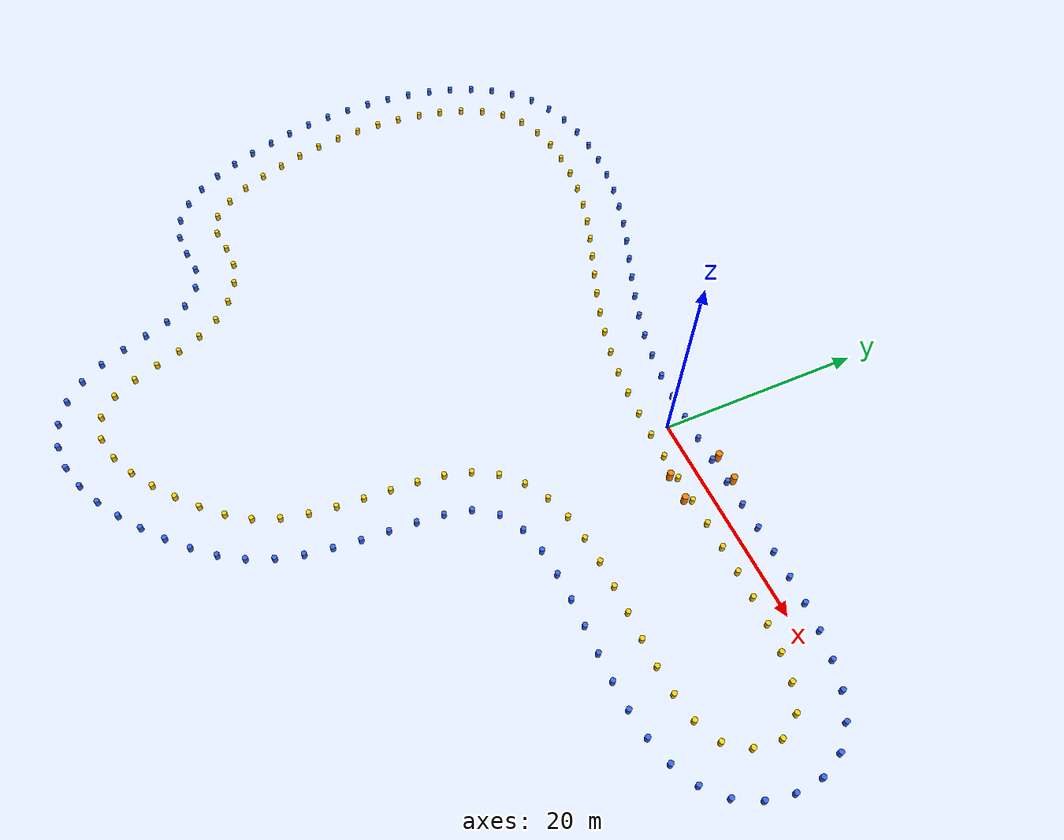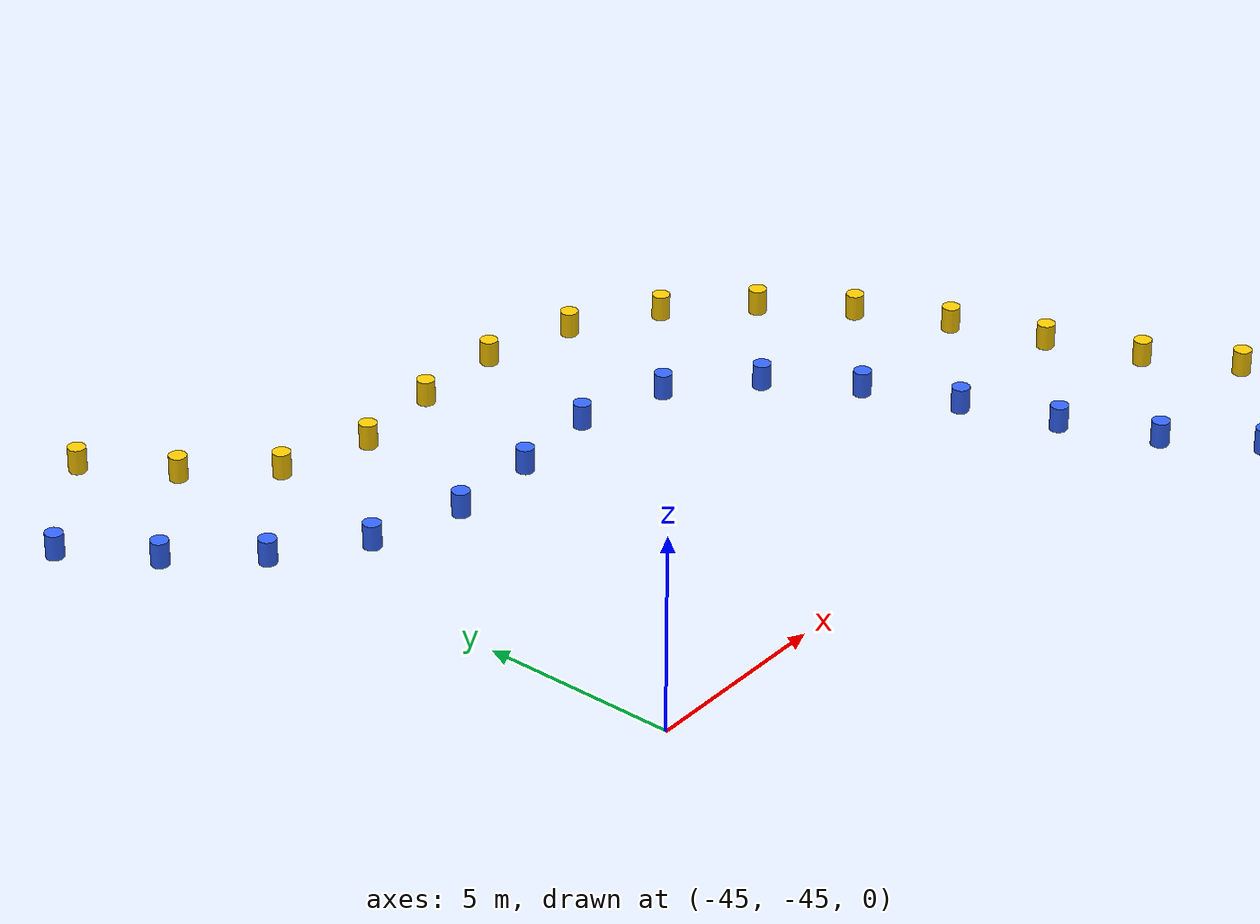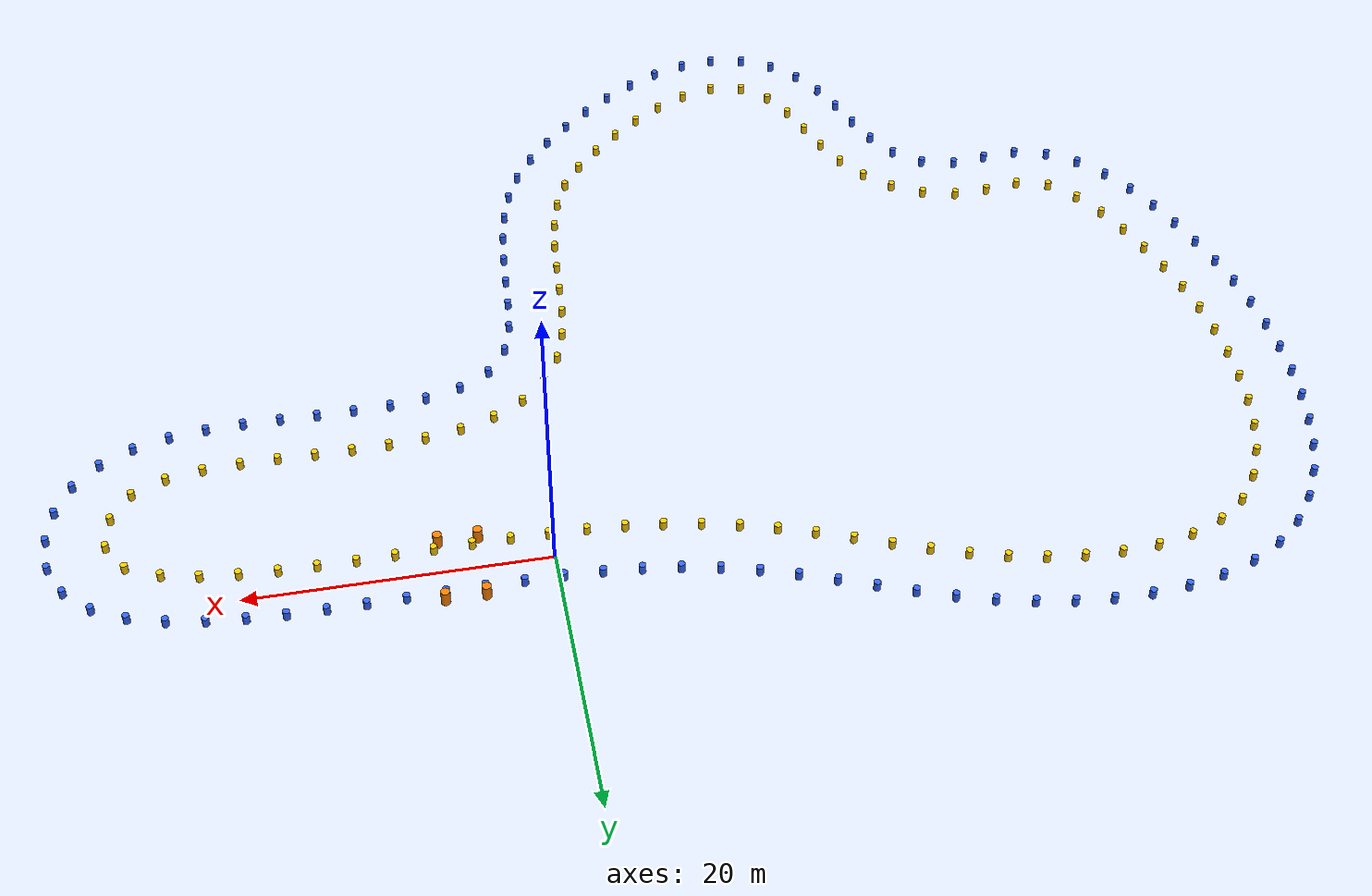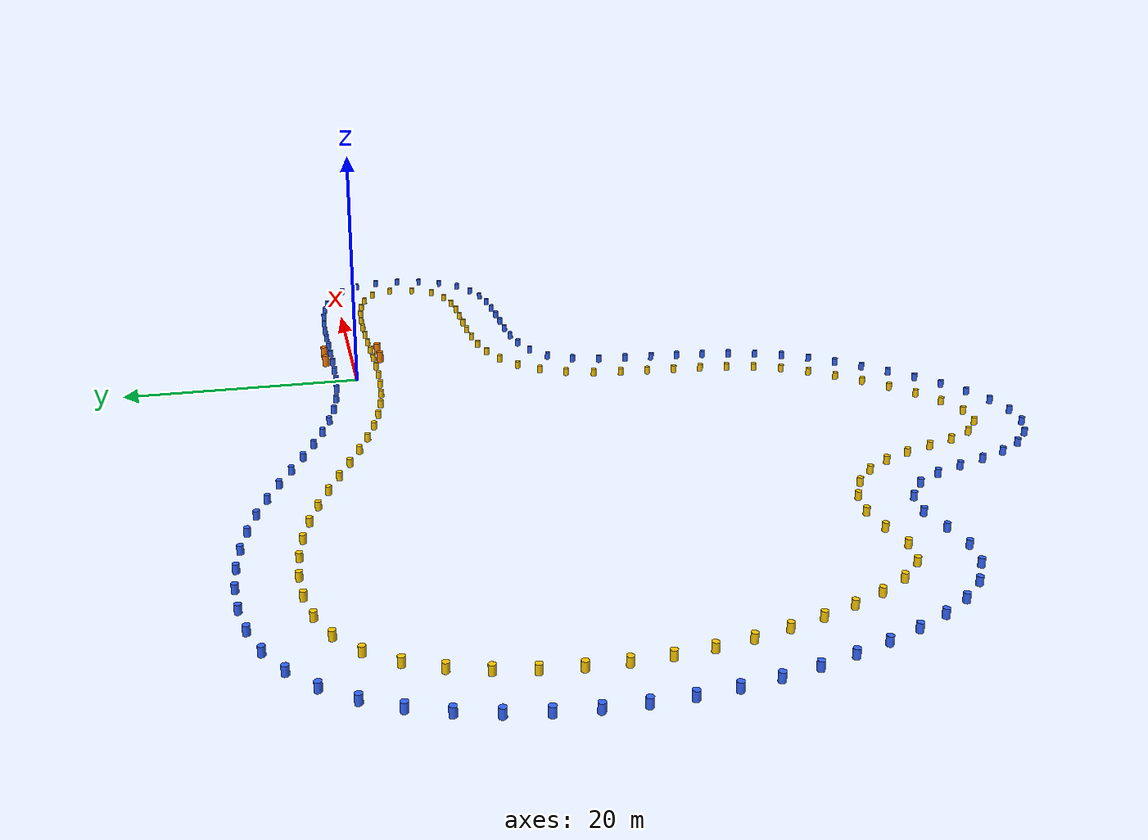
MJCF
<?xml version="1.0" ?>
<mujoco model="random_track">
  <compiler angle="radian" coordinate="local" autolimits="true"/>
  <default>
    <default class="cone">
      <joint type="free" damping="0.1" frictionloss="0.05"/>
      <geom condim="4" friction="0.5 0.005 0.0001" solref="0.02 1.0" solimp="0.99 0.99 0.001"/>
    </default>
  </default>
  <asset>
    <material name="blue_cone" rgba="0.2 0.4 1.0 1.0" specular="0.5" shininess="0.2"/>
    <material name="yellow_cone" rgba="1.0 0.8 0.0 1.0" specular="0.5" shininess="0.2"/>
    <material name="orange_cone" rgba="1.0 0.5 0.0 1.0" specular="0.5" shininess="0.2"/>
  </asset>
  <worldbody>
    <body name="cone_left_0000" pos="-31.76619228592189 -37.43387417481656 0.325">
      <joint name="cone_left_joint_0000" type="free" damping="0.1" frictionloss="0.05"/>
      <geom name="cone_left_vis_0000" type="cylinder" size="0.228 0.325" material="blue_cone" mass="1.0" density="100" condim="4" friction="0.5 0.005 0.0001" solref="0.02 1.0" solimp="0.99 0.99 0.001"/>
    </body>
    <body name="cone_left_0001" pos="-33.66527628641542 -35.84207297706479 0.325">
      <joint name="cone_left_joint_0001" type="free" damping="0.1" frictionloss="0.05"/>
      <geom name="cone_left_vis_0001" type="cylinder" size="0.228 0.325" material="blue_cone" mass="1.0" density="100" condim="4" friction="0.5 0.005 0.0001" solref="0.02 1.0" solimp="0.99 0.99 0.001"/>
    </body>
    <body name="cone_left_0002" pos="-36.04944388901805 -35.22839925791775 0.325">
      <joint name="cone_left_joint_0002" type="free" damping="0.1" frictionloss="0.05"/>
      <geom name="cone_left_vis_0002" type="cylinder" size="0.228 0.325" material="blue_cone" mass="1.0" density="100" condim="4" friction="0.5 0.005 0.0001" solref="0.02 1.0" solimp="0.99 0.99 0.001"/>
    </body>
    <body name="cone_left_0003" pos="-38.52465707860692 -35.50518306105955 0.325">
      <joint name="cone_left_joint_0003" type="free" damping="0.1" frictionloss="0.05"/>
      <geom name="cone_left_vis_0003" type="cylinder" size="0.228 0.325" material="blue_cone" mass="1.0" density="100" condim="4" friction="0.5 0.005 0.0001" solref="0.02 1.0" solimp="0.99 0.99 0.001"/>
    </body>
    <body name="cone_left_0004" pos="-41.00884921840549 -35.622648656899386 0.325">
      <joint name="cone_left_joint_0004" type="free" damping="0.1" frictionloss="0.05"/>
      <geom name="cone_left_vis_0004" type="cylinder" size="0.228 0.325" material="blue_cone" mass="1.0" density="100" condim="4" friction="0.5 0.005 0.0001" solref="0.02 1.0" solimp="0.99 0.99 0.001"/>
    </body>
    <body name="cone_left_0005" pos="-43.39758339492698 -34.96185672325035 0.325">
      <joint name="cone_left_joint_0005" type="free" damping="0.1" frictionloss="0.05"/>
      <geom name="cone_left_vis_0005" type="cylinder" size="0.228 0.325" material="blue_cone" mass="1.0" density="100" condim="4" friction="0.5 0.005 0.0001" solref="0.02 1.0" solimp="0.99 0.99 0.001"/>
    </body>
    <body name="cone_left_0006" pos="-45.441922076730194 -33.55244019775668 0.325">
      <joint name="cone_left_joint_0006" type="free" damping="0.1" frictionloss="0.05"/>
      <geom name="cone_left_vis_0006" type="cylinder" size="0.228 0.325" material="blue_cone" mass="1.0" density="100" condim="4" friction="0.5 0.005 0.0001" solref="0.02 1.0" solimp="0.99 0.99 0.001"/>
    </body>
    <body name="cone_left_0007" pos="-47.07786389364743 -31.677983943091647 0.325">
      <joint name="cone_left_joint_0007" type="free" damping="0.1" frictionloss="0.05"/>
      <geom name="cone_left_vis_0007" type="cylinder" size="0.228 0.325" material="blue_cone" mass="1.0" density="100" condim="4" friction="0.5 0.005 0.0001" solref="0.02 1.0" solimp="0.99 0.99 0.001"/>
    </body>
    <body name="cone_left_0008" pos="-48.38099265616411 -29.555775846314035 0.325">
      <joint name="cone_left_joint_0008" type="free" damping="0.1" frictionloss="0.05"/>
      <geom name="cone_left_vis_0008" type="cylinder" size="0.228 0.325" material="blue_cone" mass="1.0" density="100" condim="4" friction="0.5 0.005 0.0001" solref="0.02 1.0" solimp="0.99 0.99 0.001"/>
    </body>
    <body name="cone_left_0009" pos="-49.44105235560866 -27.30116372079158 0.325">
      <joint name="cone_left_joint_0009" type="free" damping="0.1" frictionloss="0.05"/>
      <geom name="cone_left_vis_0009" type="cylinder" size="0.228 0.325" material="blue_cone" mass="1.0" density="100" condim="4" friction="0.5 0.005 0.0001" solref="0.02 1.0" solimp="0.99 0.99 0.001"/>
    </body>
    <body name="cone_left_0010" pos="-50.32528010176412 -24.9714953919582 0.325">
      <joint name="cone_left_joint_0010" type="free" damping="0.1" frictionloss="0.05"/>
      <geom name="cone_left_vis_0010" type="cylinder" size="0.228 0.325" material="blue_cone" mass="1.0" density="100" condim="4" friction="0.5 0.005 0.0001" solref="0.02 1.0" solimp="0.99 0.99 0.001"/>
    </body>
    <body name="cone_left_0011" pos="-51.08131022367506 -22.596899475502283 0.325">
      <joint name="cone_left_joint_0011" type="free" damping="0.1" frictionloss="0.05"/>
      <geom name="cone_left_vis_0011" type="cylinder" size="0.228 0.325" material="blue_cone" mass="1.0" density="100" condim="4" friction="0.5 0.005 0.0001" solref="0.02 1.0" solimp="0.99 0.99 0.001"/>
    </body>
    <body name="cone_left_0012" pos="-51.73304245750019 -20.191592535189585 0.325">
      <joint name="cone_left_joint_0012" type="free" damping="0.1" frictionloss="0.05"/>
      <geom name="cone_left_vis_0012" type="cylinder" size="0.228 0.325" material="blue_cone" mass="1.0" density="100" condim="4" friction="0.5 0.005 0.0001" solref="0.02 1.0" solimp="0.99 0.99 0.001"/>
    </body>
    <body name="cone_left_0013" pos="-52.255216722923706 -17.755029702633422 0.325">
      <joint name="cone_left_joint_0013" type="free" damping="0.1" frictionloss="0.05"/>
      <geom name="cone_left_vis_0013" type="cylinder" size="0.228 0.325" material="blue_cone" mass="1.0" density="100" condim="4" friction="0.5 0.005 0.0001" solref="0.02 1.0" solimp="0.99 0.99 0.001"/>
    </body>
    <body name="cone_left_0014" pos="-52.62005751305296 -15.290081303679443 0.325">
      <joint name="cone_left_joint_0014" type="free" damping="0.1" frictionloss="0.05"/>
      <geom name="cone_left_vis_0014" type="cylinder" size="0.228 0.325" material="blue_cone" mass="1.0" density="100" condim="4" friction="0.5 0.005 0.0001" solref="0.02 1.0" solimp="0.99 0.99 0.001"/>
    </body>
    <body name="cone_left_0015" pos="-52.82168361253496 -12.806405533143334 0.325">
      <joint name="cone_left_joint_0015" type="free" damping="0.1" frictionloss="0.05"/>
      <geom name="cone_left_vis_0015" type="cylinder" size="0.228 0.325" material="blue_cone" mass="1.0" density="100" condim="4" friction="0.5 0.005 0.0001" solref="0.02 1.0" solimp="0.99 0.99 0.001"/>
    </body>
    <body name="cone_left_0016" pos="-52.87291729023078 -10.315031909138156 0.325">
      <joint name="cone_left_joint_0016" type="free" damping="0.1" frictionloss="0.05"/>
      <geom name="cone_left_vis_0016" type="cylinder" size="0.228 0.325" material="blue_cone" mass="1.0" density="100" condim="4" friction="0.5 0.005 0.0001" solref="0.02 1.0" solimp="0.99 0.99 0.001"/>
    </body>
    <body name="cone_left_0017" pos="-52.77394284054513 -7.825133797286185 0.325">
      <joint name="cone_left_joint_0017" type="free" damping="0.1" frictionloss="0.05"/>
      <geom name="cone_left_vis_0017" type="cylinder" size="0.228 0.325" material="blue_cone" mass="1.0" density="100" condim="4" friction="0.5 0.005 0.0001" solref="0.02 1.0" solimp="0.99 0.99 0.001"/>
    </body>
    <body name="cone_left_0018" pos="-52.51323448289681 -5.347043780936033 0.325">
      <joint name="cone_left_joint_0018" type="free" damping="0.1" frictionloss="0.05"/>
      <geom name="cone_left_vis_0018" type="cylinder" size="0.228 0.325" material="blue_cone" mass="1.0" density="100" condim="4" friction="0.5 0.005 0.0001" solref="0.02 1.0" solimp="0.99 0.99 0.001"/>
    </body>
    <body name="cone_left_0019" pos="-52.07024096131997 -2.8951429678532037 0.325">
      <joint name="cone_left_joint_0019" type="free" damping="0.1" frictionloss="0.05"/>
      <geom name="cone_left_vis_0019" type="cylinder" size="0.228 0.325" material="blue_cone" mass="1.0" density="100" condim="4" friction="0.5 0.005 0.0001" solref="0.02 1.0" solimp="0.99 0.99 0.001"/>
    </body>
    <body name="cone_left_0020" pos="-51.414305021356626 -0.491739788825555 0.325">
      <joint name="cone_left_joint_0020" type="free" damping="0.1" frictionloss="0.05"/>
      <geom name="cone_left_vis_0020" type="cylinder" size="0.228 0.325" material="blue_cone" mass="1.0" density="100" condim="4" friction="0.5 0.005 0.0001" solref="0.02 1.0" solimp="0.99 0.99 0.001"/>
    </body>
    <body name="cone_left_0021" pos="-50.50603906490181 1.827546694338622 0.325">
      <joint name="cone_left_joint_0021" type="free" damping="0.1" frictionloss="0.05"/>
      <geom name="cone_left_vis_0021" type="cylinder" size="0.228 0.325" material="blue_cone" mass="1.0" density="100" condim="4" friction="0.5 0.005 0.0001" solref="0.02 1.0" solimp="0.99 0.99 0.001"/>
    </body>
    <body name="cone_left_0022" pos="-49.299807909283146 4.005843081994357 0.325">
      <joint name="cone_left_joint_0022" type="free" damping="0.1" frictionloss="0.05"/>
      <geom name="cone_left_vis_0022" type="cylinder" size="0.228 0.325" material="blue_cone" mass="1.0" density="100" condim="4" friction="0.5 0.005 0.0001" solref="0.02 1.0" solimp="0.99 0.99 0.001"/>
    </body>
    <body name="cone_left_0023" pos="-47.75551009486766 5.95763413315855 0.325">
      <joint name="cone_left_joint_0023" type="free" damping="0.1" frictionloss="0.05"/>
      <geom name="cone_left_vis_0023" type="cylinder" size="0.228 0.325" material="blue_cone" mass="1.0" density="100" condim="4" friction="0.5 0.005 0.0001" solref="0.02 1.0" solimp="0.99 0.99 0.001"/>
    </body>
    <body name="cone_left_0024" pos="-45.86349558736276 7.57288440868075 0.325">
      <joint name="cone_left_joint_0024" type="free" damping="0.1" frictionloss="0.05"/>
      <geom name="cone_left_vis_0024" type="cylinder" size="0.228 0.325" material="blue_cone" mass="1.0" density="100" condim="4" friction="0.5 0.005 0.0001" solref="0.02 1.0" solimp="0.99 0.99 0.001"/>
    </body>
    <body name="cone_left_0025" pos="-43.68470342462422 8.775122758028061 0.325">
      <joint name="cone_left_joint_0025" type="free" damping="0.1" frictionloss="0.05"/>
      <geom name="cone_left_vis_0025" type="cylinder" size="0.228 0.325" material="blue_cone" mass="1.0" density="100" condim="4" friction="0.5 0.005 0.0001" solref="0.02 1.0" solimp="0.99 0.99 0.001"/>
    </body>
    <body name="cone_left_0026" pos="-41.33078628146646 9.58626959985601 0.325">
      <joint name="cone_left_joint_0026" type="free" damping="0.1" frictionloss="0.05"/>
      <geom name="cone_left_vis_0026" type="cylinder" size="0.228 0.325" material="blue_cone" mass="1.0" density="100" condim="4" friction="0.5 0.005 0.0001" solref="0.02 1.0" solimp="0.99 0.99 0.001"/>
    </body>
    <body name="cone_left_0027" pos="-38.8860970864303 10.062550034978656 0.325">
      <joint name="cone_left_joint_0027" type="free" damping="0.1" frictionloss="0.05"/>
      <geom name="cone_left_vis_0027" type="cylinder" size="0.228 0.325" material="blue_cone" mass="1.0" density="100" condim="4" friction="0.5 0.005 0.0001" solref="0.02 1.0" solimp="0.99 0.99 0.001"/>
    </body>
    <body name="cone_left_0028" pos="-36.40275663237617 10.260010697037998 0.325">
      <joint name="cone_left_joint_0028" type="free" damping="0.1" frictionloss="0.05"/>
      <geom name="cone_left_vis_0028" type="cylinder" size="0.228 0.325" material="blue_cone" mass="1.0" density="100" condim="4" friction="0.5 0.005 0.0001" solref="0.02 1.0" solimp="0.99 0.99 0.001"/>
    </body>
    <body name="cone_left_0029" pos="-33.911549837644955 10.223719944782516 0.325">
      <joint name="cone_left_joint_0029" type="free" damping="0.1" frictionloss="0.05"/>
      <geom name="cone_left_vis_0029" type="cylinder" size="0.228 0.325" material="blue_cone" mass="1.0" density="100" condim="4" friction="0.5 0.005 0.0001" solref="0.02 1.0" solimp="0.99 0.99 0.001"/>
    </body>
    <body name="cone_left_0030" pos="-31.431459192995575 9.98418611814607 0.325">
      <joint name="cone_left_joint_0030" type="free" damping="0.1" frictionloss="0.05"/>
      <geom name="cone_left_vis_0030" type="cylinder" size="0.228 0.325" material="blue_cone" mass="1.0" density="100" condim="4" friction="0.5 0.005 0.0001" solref="0.02 1.0" solimp="0.99 0.99 0.001"/>
    </body>
    <body name="cone_left_0031" pos="-28.976425288884755 9.55837475156656 0.325">
      <joint name="cone_left_joint_0031" type="free" damping="0.1" frictionloss="0.05"/>
      <geom name="cone_left_vis_0031" type="cylinder" size="0.228 0.325" material="blue_cone" mass="1.0" density="100" condim="4" friction="0.5 0.005 0.0001" solref="0.02 1.0" solimp="0.99 0.99 0.001"/>
    </body>
    <body name="cone_left_0032" pos="-26.558252968306064 8.957242334367649 0.325">
      <joint name="cone_left_joint_0032" type="free" damping="0.1" frictionloss="0.05"/>
      <geom name="cone_left_vis_0032" type="cylinder" size="0.228 0.325" material="blue_cone" mass="1.0" density="100" condim="4" friction="0.5 0.005 0.0001" solref="0.02 1.0" solimp="0.99 0.99 0.001"/>
    </body>
    <body name="cone_left_0033" pos="-24.18258922787585 8.204943253523183 0.325">
      <joint name="cone_left_joint_0033" type="free" damping="0.1" frictionloss="0.05"/>
      <geom name="cone_left_vis_0033" type="cylinder" size="0.228 0.325" material="blue_cone" mass="1.0" density="100" condim="4" friction="0.5 0.005 0.0001" solref="0.02 1.0" solimp="0.99 0.99 0.001"/>
    </body>
    <body name="cone_left_0034" pos="-21.845401475498534 7.33997820114466 0.325">
      <joint name="cone_left_joint_0034" type="free" damping="0.1" frictionloss="0.05"/>
      <geom name="cone_left_vis_0034" type="cylinder" size="0.228 0.325" material="blue_cone" mass="1.0" density="100" condim="4" friction="0.5 0.005 0.0001" solref="0.02 1.0" solimp="0.99 0.99 0.001"/>
    </body>
    <body name="cone_left_0035" pos="-19.53299785037322 6.4104473102925255 0.325">
      <joint name="cone_left_joint_0035" type="free" damping="0.1" frictionloss="0.05"/>
      <geom name="cone_left_vis_0035" type="cylinder" size="0.228 0.325" material="blue_cone" mass="1.0" density="100" condim="4" friction="0.5 0.005 0.0001" solref="0.02 1.0" solimp="0.99 0.99 0.001"/>
    </body>
    <body name="cone_left_0036" pos="-17.22521540517232 5.469437010779572 0.325">
      <joint name="cone_left_joint_0036" type="free" damping="0.1" frictionloss="0.05"/>
      <geom name="cone_left_vis_0036" type="cylinder" size="0.228 0.325" material="blue_cone" mass="1.0" density="100" condim="4" friction="0.5 0.005 0.0001" solref="0.02 1.0" solimp="0.99 0.99 0.001"/>
    </body>
    <body name="cone_left_0037" pos="-14.900768270841809 4.5706125437887835 0.325">
      <joint name="cone_left_joint_0037" type="free" damping="0.1" frictionloss="0.05"/>
      <geom name="cone_left_vis_0037" type="cylinder" size="0.228 0.325" material="blue_cone" mass="1.0" density="100" condim="4" friction="0.5 0.005 0.0001" solref="0.02 1.0" solimp="0.99 0.99 0.001"/>
    </body>
    <body name="cone_left_0038" pos="-12.54322164721107 3.7630530491820195 0.325">
      <joint name="cone_left_joint_0038" type="free" damping="0.1" frictionloss="0.05"/>
      <geom name="cone_left_vis_0038" type="cylinder" size="0.228 0.325" material="blue_cone" mass="1.0" density="100" condim="4" friction="0.5 0.005 0.0001" solref="0.02 1.0" solimp="0.99 0.99 0.001"/>
    </body>
    <body name="cone_left_0039" pos="-10.144957970588521 3.0864760989741598 0.325">
      <joint name="cone_left_joint_0039" type="free" damping="0.1" frictionloss="0.05"/>
      <geom name="cone_left_vis_0039" type="cylinder" size="0.228 0.325" material="blue_cone" mass="1.0" density="100" condim="4" friction="0.5 0.005 0.0001" solref="0.02 1.0" solimp="0.99 0.99 0.001"/>
    </body>
    <body name="cone_left_0040" pos="-7.7079892829310666 2.5666863890501475 0.325">
      <joint name="cone_left_joint_0040" type="free" damping="0.1" frictionloss="0.05"/>
      <geom name="cone_left_vis_0040" type="cylinder" size="0.228 0.325" material="blue_cone" mass="1.0" density="100" condim="4" friction="0.5 0.005 0.0001" solref="0.02 1.0" solimp="0.99 0.99 0.001"/>
    </body>
    <body name="cone_left_0041" pos="-5.241188876274379 2.2146818120780836 0.325">
      <joint name="cone_left_joint_0041" type="free" damping="0.1" frictionloss="0.05"/>
      <geom name="cone_left_vis_0041" type="cylinder" size="0.228 0.325" material="blue_cone" mass="1.0" density="100" condim="4" friction="0.5 0.005 0.0001" solref="0.02 1.0" solimp="0.99 0.99 0.001"/>
    </body>
    <body name="cone_left_0042" pos="-2.757605319067167 2.0099148140899246 0.325">
      <joint name="cone_left_joint_0042" type="free" damping="0.1" frictionloss="0.05"/>
      <geom name="cone_left_vis_0042" type="cylinder" size="0.228 0.325" material="blue_cone" mass="1.0" density="100" condim="4" friction="0.5 0.005 0.0001" solref="0.02 1.0" solimp="0.99 0.99 0.001"/>
    </body>
    <body name="cone_left_0043" pos="-0.26758687283570737 1.9069309904014915 0.325">
      <joint name="cone_left_joint_0043" type="free" damping="0.1" frictionloss="0.05"/>
      <geom name="cone_left_vis_0043" type="cylinder" size="0.228 0.325" material="blue_cone" mass="1.0" density="100" condim="4" friction="0.5 0.005 0.0001" solref="0.02 1.0" solimp="0.99 0.99 0.001"/>
    </body>
    <body name="cone_left_0044" pos="2.2243954064409195 1.8730182728461813 0.325">
      <joint name="cone_left_joint_0044" type="free" damping="0.1" frictionloss="0.05"/>
      <geom name="cone_left_vis_0044" type="cylinder" size="0.228 0.325" material="blue_cone" mass="1.0" density="100" condim="4" friction="0.5 0.005 0.0001" solref="0.02 1.0" solimp="0.99 0.99 0.001"/>
    </body>
    <body name="cone_left_0045" pos="4.7166178181932565 1.8837510540027722 0.325">
      <joint name="cone_left_joint_0045" type="free" damping="0.1" frictionloss="0.05"/>
      <geom name="cone_left_vis_0045" type="cylinder" size="0.228 0.325" material="blue_cone" mass="1.0" density="100" condim="4" friction="0.5 0.005 0.0001" solref="0.02 1.0" solimp="0.99 0.99 0.001"/>
    </body>
    <body name="cone_left_0046" pos="7.208620017110249 1.91968258357538 0.325">
      <joint name="cone_left_joint_0046" type="free" damping="0.1" frictionloss="0.05"/>
      <geom name="cone_left_vis_0046" type="cylinder" size="0.228 0.325" material="blue_cone" mass="1.0" density="100" condim="4" friction="0.5 0.005 0.0001" solref="0.02 1.0" solimp="0.99 0.99 0.001"/>
    </body>
    <body name="cone_left_0047" pos="9.700502130808502 1.9634047398022858 0.325">
      <joint name="cone_left_joint_0047" type="free" damping="0.1" frictionloss="0.05"/>
      <geom name="cone_left_vis_0047" type="cylinder" size="0.228 0.325" material="blue_cone" mass="1.0" density="100" condim="4" friction="0.5 0.005 0.0001" solref="0.02 1.0" solimp="0.99 0.99 0.001"/>
    </body>
    <body name="cone_left_0048" pos="12.192524483818346 1.9978222802206886 0.325">
      <joint name="cone_left_joint_0048" type="free" damping="0.1" frictionloss="0.05"/>
      <geom name="cone_left_vis_0048" type="cylinder" size="0.228 0.325" material="blue_cone" mass="1.0" density="100" condim="4" friction="0.5 0.005 0.0001" solref="0.02 1.0" solimp="0.99 0.99 0.001"/>
    </body>
    <body name="cone_left_0049" pos="14.684756670905358 2.0044078427400365 0.325">
      <joint name="cone_left_joint_0049" type="free" damping="0.1" frictionloss="0.05"/>
      <geom name="cone_left_vis_0049" type="cylinder" size="0.228 0.325" material="blue_cone" mass="1.0" density="100" condim="4" friction="0.5 0.005 0.0001" solref="0.02 1.0" solimp="0.99 0.99 0.001"/>
    </body>
    <body name="cone_left_0050" pos="17.17657275234467 1.96081247985461 0.325">
      <joint name="cone_left_joint_0050" type="free" damping="0.1" frictionloss="0.05"/>
      <geom name="cone_left_vis_0050" type="cylinder" size="0.228 0.325" material="blue_cone" mass="1.0" density="100" condim="4" friction="0.5 0.005 0.0001" solref="0.02 1.0" solimp="0.99 0.99 0.001"/>
    </body>
    <body name="cone_left_0051" pos="19.66563417090356 1.8377249684181436 0.325">
      <joint name="cone_left_joint_0051" type="free" damping="0.1" frictionloss="0.05"/>
      <geom name="cone_left_vis_0051" type="cylinder" size="0.228 0.325" material="blue_cone" mass="1.0" density="100" condim="4" friction="0.5 0.005 0.0001" solref="0.02 1.0" solimp="0.99 0.99 0.001"/>
    </body>
    <body name="cone_left_0052" pos="22.145478359152236 1.5930384417003154 0.325">
      <joint name="cone_left_joint_0052" type="free" damping="0.1" frictionloss="0.05"/>
      <geom name="cone_left_vis_0052" type="cylinder" size="0.228 0.325" material="blue_cone" mass="1.0" density="100" condim="4" friction="0.5 0.005 0.0001" solref="0.02 1.0" solimp="0.99 0.99 0.001"/>
    </body>
    <body name="cone_left_0053" pos="24.59926795094148 1.1620874140443362 0.325">
      <joint name="cone_left_joint_0053" type="free" damping="0.1" frictionloss="0.05"/>
      <geom name="cone_left_vis_0053" type="cylinder" size="0.228 0.325" material="blue_cone" mass="1.0" density="100" condim="4" friction="0.5 0.005 0.0001" solref="0.02 1.0" solimp="0.99 0.99 0.001"/>
    </body>
    <body name="cone_left_0054" pos="26.98248654566831 0.4411369767054083 0.325">
      <joint name="cone_left_joint_0054" type="free" damping="0.1" frictionloss="0.05"/>
      <geom name="cone_left_vis_0054" type="cylinder" size="0.228 0.325" material="blue_cone" mass="1.0" density="100" condim="4" friction="0.5 0.005 0.0001" solref="0.02 1.0" solimp="0.99 0.99 0.001"/>
    </body>
    <body name="cone_left_0055" pos="29.178929674752965 -0.7235105832301088 0.325">
      <joint name="cone_left_joint_0055" type="free" damping="0.1" frictionloss="0.05"/>
      <geom name="cone_left_vis_0055" type="cylinder" size="0.228 0.325" material="blue_cone" mass="1.0" density="100" condim="4" friction="0.5 0.005 0.0001" solref="0.02 1.0" solimp="0.99 0.99 0.001"/>
    </body>
    <body name="cone_left_0056" pos="30.93437710836477 -2.4748195821556322 0.325">
      <joint name="cone_left_joint_0056" type="free" damping="0.1" frictionloss="0.05"/>
      <geom name="cone_left_vis_0056" type="cylinder" size="0.228 0.325" material="blue_cone" mass="1.0" density="100" condim="4" friction="0.5 0.005 0.0001" solref="0.02 1.0" solimp="0.99 0.99 0.001"/>
    </body>
    <body name="cone_left_0057" pos="31.926630854964884 -4.744328542619854 0.325">
      <joint name="cone_left_joint_0057" type="free" damping="0.1" frictionloss="0.05"/>
      <geom name="cone_left_vis_0057" type="cylinder" size="0.228 0.325" material="blue_cone" mass="1.0" density="100" condim="4" friction="0.5 0.005 0.0001" solref="0.02 1.0" solimp="0.99 0.99 0.001"/>
    </body>
    <body name="cone_left_0058" pos="32.071939857809895 -7.222219797475546 0.325">
      <joint name="cone_left_joint_0058" type="free" damping="0.1" frictionloss="0.05"/>
      <geom name="cone_left_vis_0058" type="cylinder" size="0.228 0.325" material="blue_cone" mass="1.0" density="100" condim="4" friction="0.5 0.005 0.0001" solref="0.02 1.0" solimp="0.99 0.99 0.001"/>
    </body>
    <body name="cone_left_0059" pos="31.57018149410598 -9.658081494595919 0.325">
      <joint name="cone_left_joint_0059" type="free" damping="0.1" frictionloss="0.05"/>
      <geom name="cone_left_vis_0059" type="cylinder" size="0.228 0.325" material="blue_cone" mass="1.0" density="100" condim="4" friction="0.5 0.005 0.0001" solref="0.02 1.0" solimp="0.99 0.99 0.001"/>
    </body>
    <body name="cone_left_0060" pos="30.44837983453027 -11.872473445574215 0.325">
      <joint name="cone_left_joint_0060" type="free" damping="0.1" frictionloss="0.05"/>
      <geom name="cone_left_vis_0060" type="cylinder" size="0.228 0.325" material="blue_cone" mass="1.0" density="100" condim="4" friction="0.5 0.005 0.0001" solref="0.02 1.0" solimp="0.99 0.99 0.001"/>
    </body>
    <body name="cone_left_0061" pos="28.684613650641467 -13.61787754196365 0.325">
      <joint name="cone_left_joint_0061" type="free" damping="0.1" frictionloss="0.05"/>
      <geom name="cone_left_vis_0061" type="cylinder" size="0.228 0.325" material="blue_cone" mass="1.0" density="100" condim="4" friction="0.5 0.005 0.0001" solref="0.02 1.0" solimp="0.99 0.99 0.001"/>
    </body>
    <body name="cone_left_0062" pos="26.48448031716984 -14.773527953461397 0.325">
      <joint name="cone_left_joint_0062" type="free" damping="0.1" frictionloss="0.05"/>
      <geom name="cone_left_vis_0062" type="cylinder" size="0.228 0.325" material="blue_cone" mass="1.0" density="100" condim="4" friction="0.5 0.005 0.0001" solref="0.02 1.0" solimp="0.99 0.99 0.001"/>
    </body>
    <body name="cone_left_0063" pos="24.08252573048503 -15.426221153253493 0.325">
      <joint name="cone_left_joint_0063" type="free" damping="0.1" frictionloss="0.05"/>
      <geom name="cone_left_vis_0063" type="cylinder" size="0.228 0.325" material="blue_cone" mass="1.0" density="100" condim="4" friction="0.5 0.005 0.0001" solref="0.02 1.0" solimp="0.99 0.99 0.001"/>
    </body>
    <body name="cone_left_0064" pos="21.611054708569554 -15.737898828276585 0.325">
      <joint name="cone_left_joint_0064" type="free" damping="0.1" frictionloss="0.05"/>
      <geom name="cone_left_vis_0064" type="cylinder" size="0.228 0.325" material="blue_cone" mass="1.0" density="100" condim="4" friction="0.5 0.005 0.0001" solref="0.02 1.0" solimp="0.99 0.99 0.001"/>
    </body>
    <body name="cone_left_0065" pos="19.121419441668223 -15.843303654725176 0.325">
      <joint name="cone_left_joint_0065" type="free" damping="0.1" frictionloss="0.05"/>
      <geom name="cone_left_vis_0065" type="cylinder" size="0.228 0.325" material="blue_cone" mass="1.0" density="100" condim="4" friction="0.5 0.005 0.0001" solref="0.02 1.0" solimp="0.99 0.99 0.001"/>
    </body>
    <body name="cone_left_0066" pos="16.62924899151895 -15.837830080602416 0.325">
      <joint name="cone_left_joint_0066" type="free" damping="0.1" frictionloss="0.05"/>
      <geom name="cone_left_vis_0066" type="cylinder" size="0.228 0.325" material="blue_cone" mass="1.0" density="100" condim="4" friction="0.5 0.005 0.0001" solref="0.02 1.0" solimp="0.99 0.99 0.001"/>
    </body>
    <body name="cone_left_0067" pos="14.137382159952296 -15.793345298204514 0.325">
      <joint name="cone_left_joint_0067" type="free" damping="0.1" frictionloss="0.05"/>
      <geom name="cone_left_vis_0067" type="cylinder" size="0.228 0.325" material="blue_cone" mass="1.0" density="100" condim="4" friction="0.5 0.005 0.0001" solref="0.02 1.0" solimp="0.99 0.99 0.001"/>
    </body>
    <body name="cone_left_0068" pos="11.645250444091687 -15.773845496737394 0.325">
      <joint name="cone_left_joint_0068" type="free" damping="0.1" frictionloss="0.05"/>
      <geom name="cone_left_vis_0068" type="cylinder" size="0.228 0.325" material="blue_cone" mass="1.0" density="100" condim="4" friction="0.5 0.005 0.0001" solref="0.02 1.0" solimp="0.99 0.99 0.001"/>
    </body>
    <body name="cone_left_0069" pos="9.154467397396019 -15.849897979712992 0.325">
      <joint name="cone_left_joint_0069" type="free" damping="0.1" frictionloss="0.05"/>
      <geom name="cone_left_vis_0069" type="cylinder" size="0.228 0.325" material="blue_cone" mass="1.0" density="100" condim="4" friction="0.5 0.005 0.0001" solref="0.02 1.0" solimp="0.99 0.99 0.001"/>
    </body>
    <body name="cone_left_0070" pos="6.678032051030783 -16.11994949364548 0.325">
      <joint name="cone_left_joint_0070" type="free" damping="0.1" frictionloss="0.05"/>
      <geom name="cone_left_vis_0070" type="cylinder" size="0.228 0.325" material="blue_cone" mass="1.0" density="100" condim="4" friction="0.5 0.005 0.0001" solref="0.02 1.0" solimp="0.99 0.99 0.001"/>
    </body>
    <body name="cone_left_0071" pos="4.270644771906532 -16.74878929952945 0.325">
      <joint name="cone_left_joint_0071" type="free" damping="0.1" frictionloss="0.05"/>
      <geom name="cone_left_vis_0071" type="cylinder" size="0.228 0.325" material="blue_cone" mass="1.0" density="100" condim="4" friction="0.5 0.005 0.0001" solref="0.02 1.0" solimp="0.99 0.99 0.001"/>
    </body>
    <body name="cone_left_0072" pos="2.142084297204377 -18.01639795783936 0.325">
      <joint name="cone_left_joint_0072" type="free" damping="0.1" frictionloss="0.05"/>
      <geom name="cone_left_vis_0072" type="cylinder" size="0.228 0.325" material="blue_cone" mass="1.0" density="100" condim="4" friction="0.5 0.005 0.0001" solref="0.02 1.0" solimp="0.99 0.99 0.001"/>
    </body>
    <body name="cone_left_0073" pos="0.7532546071503958 -20.061161430172646 0.325">
      <joint name="cone_left_joint_0073" type="free" damping="0.1" frictionloss="0.05"/>
      <geom name="cone_left_vis_0073" type="cylinder" size="0.228 0.325" material="blue_cone" mass="1.0" density="100" condim="4" friction="0.5 0.005 0.0001" solref="0.02 1.0" solimp="0.99 0.99 0.001"/>
    </body>
    <body name="cone_left_0074" pos="0.14703017833210197 -22.47220700739969 0.325">
      <joint name="cone_left_joint_0074" type="free" damping="0.1" frictionloss="0.05"/>
      <geom name="cone_left_vis_0074" type="cylinder" size="0.228 0.325" material="blue_cone" mass="1.0" density="100" condim="4" friction="0.5 0.005 0.0001" solref="0.02 1.0" solimp="0.99 0.99 0.001"/>
    </body>
    <body name="cone_left_0075" pos="-0.10148998752620741 -24.951575898692766 0.325">
      <joint name="cone_left_joint_0075" type="free" damping="0.1" frictionloss="0.05"/>
      <geom name="cone_left_vis_0075" type="cylinder" size="0.228 0.325" material="blue_cone" mass="1.0" density="100" condim="4" friction="0.5 0.005 0.0001" solref="0.02 1.0" solimp="0.99 0.99 0.001"/>
    </body>
    <body name="cone_left_0076" pos="-0.2652299210522955 -27.438437097731395 0.325">
      <joint name="cone_left_joint_0076" type="free" damping="0.1" frictionloss="0.05"/>
      <geom name="cone_left_vis_0076" type="cylinder" size="0.228 0.325" material="blue_cone" mass="1.0" density="100" condim="4" friction="0.5 0.005 0.0001" solref="0.02 1.0" solimp="0.99 0.99 0.001"/>
    </body>
    <body name="cone_left_0077" pos="-0.43384953128988 -29.924961153361266 0.325">
      <joint name="cone_left_joint_0077" type="free" damping="0.1" frictionloss="0.05"/>
      <geom name="cone_left_vis_0077" type="cylinder" size="0.228 0.325" material="blue_cone" mass="1.0" density="100" condim="4" friction="0.5 0.005 0.0001" solref="0.02 1.0" solimp="0.99 0.99 0.001"/>
    </body>
    <body name="cone_left_0078" pos="-0.6810857537614226 -32.4047021420003 0.325">
      <joint name="cone_left_joint_0078" type="free" damping="0.1" frictionloss="0.05"/>
      <geom name="cone_left_vis_0078" type="cylinder" size="0.228 0.325" material="blue_cone" mass="1.0" density="100" condim="4" friction="0.5 0.005 0.0001" solref="0.02 1.0" solimp="0.99 0.99 0.001"/>
    </body>
    <body name="cone_left_0079" pos="-1.0827622267207317 -34.863724146528604 0.325">
      <joint name="cone_left_joint_0079" type="free" damping="0.1" frictionloss="0.05"/>
      <geom name="cone_left_vis_0079" type="cylinder" size="0.228 0.325" material="blue_cone" mass="1.0" density="100" condim="4" friction="0.5 0.005 0.0001" solref="0.02 1.0" solimp="0.99 0.99 0.001"/>
    </body>
    <body name="cone_left_0080" pos="-1.7206657362025766 -37.271538361887885 0.325">
      <joint name="cone_left_joint_0080" type="free" damping="0.1" frictionloss="0.05"/>
      <geom name="cone_left_vis_0080" type="cylinder" size="0.228 0.325" material="blue_cone" mass="1.0" density="100" condim="4" friction="0.5 0.005 0.0001" solref="0.02 1.0" solimp="0.99 0.99 0.001"/>
    </body>
    <body name="cone_left_0081" pos="-2.671940908603034 -39.572524427728254 0.325">
      <joint name="cone_left_joint_0081" type="free" damping="0.1" frictionloss="0.05"/>
      <geom name="cone_left_vis_0081" type="cylinder" size="0.228 0.325" material="blue_cone" mass="1.0" density="100" condim="4" friction="0.5 0.005 0.0001" solref="0.02 1.0" solimp="0.99 0.99 0.001"/>
    </body>
    <body name="cone_left_0082" pos="-3.9774106915411522 -41.692448976782984 0.325">
      <joint name="cone_left_joint_0082" type="free" damping="0.1" frictionloss="0.05"/>
      <geom name="cone_left_vis_0082" type="cylinder" size="0.228 0.325" material="blue_cone" mass="1.0" density="100" condim="4" friction="0.5 0.005 0.0001" solref="0.02 1.0" solimp="0.99 0.99 0.001"/>
    </body>
    <body name="cone_left_0083" pos="-5.55712396614733 -43.61851542397577 0.325">
      <joint name="cone_left_joint_0083" type="free" damping="0.1" frictionloss="0.05"/>
      <geom name="cone_left_vis_0083" type="cylinder" size="0.228 0.325" material="blue_cone" mass="1.0" density="100" condim="4" friction="0.5 0.005 0.0001" solref="0.02 1.0" solimp="0.99 0.99 0.001"/>
    </body>
    <body name="cone_left_0084" pos="-7.29341731360536 -45.40587333934094 0.325">
      <joint name="cone_left_joint_0084" type="free" damping="0.1" frictionloss="0.05"/>
      <geom name="cone_left_vis_0084" type="cylinder" size="0.228 0.325" material="blue_cone" mass="1.0" density="100" condim="4" friction="0.5 0.005 0.0001" solref="0.02 1.0" solimp="0.99 0.99 0.001"/>
    </body>
    <body name="cone_left_0085" pos="-9.135760695874879 -47.08369401689289 0.325">
      <joint name="cone_left_joint_0085" type="free" damping="0.1" frictionloss="0.05"/>
      <geom name="cone_left_vis_0085" type="cylinder" size="0.228 0.325" material="blue_cone" mass="1.0" density="100" condim="4" friction="0.5 0.005 0.0001" solref="0.02 1.0" solimp="0.99 0.99 0.001"/>
    </body>
    <body name="cone_left_0086" pos="-11.089145117478637 -48.63053448004767 0.325">
      <joint name="cone_left_joint_0086" type="free" damping="0.1" frictionloss="0.05"/>
      <geom name="cone_left_vis_0086" type="cylinder" size="0.228 0.325" material="blue_cone" mass="1.0" density="100" condim="4" friction="0.5 0.005 0.0001" solref="0.02 1.0" solimp="0.99 0.99 0.001"/>
    </body>
    <body name="cone_left_0087" pos="-13.167209254584463 -50.00464609082043 0.325">
      <joint name="cone_left_joint_0087" type="free" damping="0.1" frictionloss="0.05"/>
      <geom name="cone_left_vis_0087" type="cylinder" size="0.228 0.325" material="blue_cone" mass="1.0" density="100" condim="4" friction="0.5 0.005 0.0001" solref="0.02 1.0" solimp="0.99 0.99 0.001"/>
    </body>
    <body name="cone_left_0088" pos="-15.38646998382103 -51.13481869398808 0.325">
      <joint name="cone_left_joint_0088" type="free" damping="0.1" frictionloss="0.05"/>
      <geom name="cone_left_vis_0088" type="cylinder" size="0.228 0.325" material="blue_cone" mass="1.0" density="100" condim="4" friction="0.5 0.005 0.0001" solref="0.02 1.0" solimp="0.99 0.99 0.001"/>
    </body>
    <body name="cone_left_0089" pos="-17.753358217128223 -51.903784014524014 0.325">
      <joint name="cone_left_joint_0089" type="free" damping="0.1" frictionloss="0.05"/>
      <geom name="cone_left_vis_0089" type="cylinder" size="0.228 0.325" material="blue_cone" mass="1.0" density="100" condim="4" friction="0.5 0.005 0.0001" solref="0.02 1.0" solimp="0.99 0.99 0.001"/>
    </body>
    <body name="cone_left_0090" pos="-20.227585149107682 -52.13952939927349 0.325">
      <joint name="cone_left_joint_0090" type="free" damping="0.1" frictionloss="0.05"/>
      <geom name="cone_left_vis_0090" type="cylinder" size="0.228 0.325" material="blue_cone" mass="1.0" density="100" condim="4" friction="0.5 0.005 0.0001" solref="0.02 1.0" solimp="0.99 0.99 0.001"/>
    </body>
    <body name="cone_left_0091" pos="-22.66410521309814 -51.66663765840239 0.325">
      <joint name="cone_left_joint_0091" type="free" damping="0.1" frictionloss="0.05"/>
      <geom name="cone_left_vis_0091" type="cylinder" size="0.228 0.325" material="blue_cone" mass="1.0" density="100" condim="4" friction="0.5 0.005 0.0001" solref="0.02 1.0" solimp="0.99 0.99 0.001"/>
    </body>
    <body name="cone_left_0092" pos="-24.8300659630694 -50.45429194387541 0.325">
      <joint name="cone_left_joint_0092" type="free" damping="0.1" frictionloss="0.05"/>
      <geom name="cone_left_vis_0092" type="cylinder" size="0.228 0.325" material="blue_cone" mass="1.0" density="100" condim="4" friction="0.5 0.005 0.0001" solref="0.02 1.0" solimp="0.99 0.99 0.001"/>
    </body>
    <body name="cone_left_0093" pos="-26.578859745649666 -48.68850406161942 0.325">
      <joint name="cone_left_joint_0093" type="free" damping="0.1" frictionloss="0.05"/>
      <geom name="cone_left_vis_0093" type="cylinder" size="0.228 0.325" material="blue_cone" mass="1.0" density="100" condim="4" friction="0.5 0.005 0.0001" solref="0.02 1.0" solimp="0.99 0.99 0.001"/>
    </body>
    <body name="cone_left_0094" pos="-27.872328017832928 -46.56320148316362 0.325">
      <joint name="cone_left_joint_0094" type="free" damping="0.1" frictionloss="0.05"/>
      <geom name="cone_left_vis_0094" type="cylinder" size="0.228 0.325" material="blue_cone" mass="1.0" density="100" condim="4" friction="0.5 0.005 0.0001" solref="0.02 1.0" solimp="0.99 0.99 0.001"/>
    </body>
    <body name="cone_left_0095" pos="-28.814197601281293 -44.257216873982195 0.325">
      <joint name="cone_left_joint_0095" type="free" damping="0.1" frictionloss="0.05"/>
      <geom name="cone_left_vis_0095" type="cylinder" size="0.228 0.325" material="blue_cone" mass="1.0" density="100" condim="4" friction="0.5 0.005 0.0001" solref="0.02 1.0" solimp="0.99 0.99 0.001"/>
    </body>
    <body name="cone_left_0096" pos="-29.604471492045306 -41.8936124875733 0.325">
      <joint name="cone_left_joint_0096" type="free" damping="0.1" frictionloss="0.05"/>
      <geom name="cone_left_vis_0096" type="cylinder" size="0.228 0.325" material="blue_cone" mass="1.0" density="100" condim="4" friction="0.5 0.005 0.0001" solref="0.02 1.0" solimp="0.99 0.99 0.001"/>
    </body>
    <body name="cone_left_0097" pos="-30.486487033095372 -39.563776184258785 0.325">
      <joint name="cone_left_joint_0097" type="free" damping="0.1" frictionloss="0.05"/>
      <geom name="cone_left_vis_0097" type="cylinder" size="0.228 0.325" material="blue_cone" mass="1.0" density="100" condim="4" friction="0.5 0.005 0.0001" solref="0.02 1.0" solimp="0.99 0.99 0.001"/>
    </body>
    <body name="cone_right_0000" pos="-28.823688884088767 -35.03199242401537 0.325">
      <joint name="cone_right_joint_0000" type="free" damping="0.1" frictionloss="0.05"/>
      <geom name="cone_right_vis_0000" type="cylinder" size="0.228 0.325" material="yellow_cone" mass="1.0" condim="4" friction="0.5 0.005 0.0001"/>
    </body>
    <body name="cone_right_0001" pos="-30.601530645563884 -33.31684783537831 0.325">
      <joint name="cone_right_joint_0001" type="free" damping="0.1" frictionloss="0.05"/>
      <geom name="cone_right_vis_0001" type="cylinder" size="0.228 0.325" material="yellow_cone" mass="1.0" condim="4" friction="0.5 0.005 0.0001"/>
    </body>
    <body name="cone_right_0002" pos="-32.736645275523784 -32.076439091027225 0.325">
      <joint name="cone_right_joint_0002" type="free" damping="0.1" frictionloss="0.05"/>
      <geom name="cone_right_vis_0002" type="cylinder" size="0.228 0.325" material="yellow_cone" mass="1.0" condim="4" friction="0.5 0.005 0.0001"/>
    </body>
    <body name="cone_right_0003" pos="-35.12654892760504 -31.465756266373532 0.325">
      <joint name="cone_right_joint_0003" type="free" damping="0.1" frictionloss="0.05"/>
      <geom name="cone_right_vis_0003" type="cylinder" size="0.228 0.325" material="yellow_cone" mass="1.0" condim="4" friction="0.5 0.005 0.0001"/>
    </body>
    <body name="cone_right_0004" pos="-37.59638778192031 -31.54133183248313 0.325">
      <joint name="cone_right_joint_0004" type="free" damping="0.1" frictionloss="0.05"/>
      <geom name="cone_right_vis_0004" type="cylinder" size="0.228 0.325" material="yellow_cone" mass="1.0" condim="4" friction="0.5 0.005 0.0001"/>
    </body>
    <body name="cone_right_0005" pos="-40.05326596119397 -31.8429289570648 0.325">
      <joint name="cone_right_joint_0005" type="free" damping="0.1" frictionloss="0.05"/>
      <geom name="cone_right_vis_0005" type="cylinder" size="0.228 0.325" material="yellow_cone" mass="1.0" condim="4" friction="0.5 0.005 0.0001"/>
    </body>
    <body name="cone_right_0006" pos="-42.37584088131706 -31.161086356607292 0.325">
      <joint name="cone_right_joint_0006" type="free" damping="0.1" frictionloss="0.05"/>
      <geom name="cone_right_vis_0006" type="cylinder" size="0.228 0.325" material="yellow_cone" mass="1.0" condim="4" friction="0.5 0.005 0.0001"/>
    </body>
    <body name="cone_right_0007" pos="-44.06149994030851 -29.362600962191436 0.325">
      <joint name="cone_right_joint_0007" type="free" damping="0.1" frictionloss="0.05"/>
      <geom name="cone_right_vis_0007" type="cylinder" size="0.228 0.325" material="yellow_cone" mass="1.0" condim="4" friction="0.5 0.005 0.0001"/>
    </body>
    <body name="cone_right_0008" pos="-45.30556402488898 -27.224615683896246 0.325">
      <joint name="cone_right_joint_0008" type="free" damping="0.1" frictionloss="0.05"/>
      <geom name="cone_right_vis_0008" type="cylinder" size="0.228 0.325" material="yellow_cone" mass="1.0" condim="4" friction="0.5 0.005 0.0001"/>
    </body>
    <body name="cone_right_0009" pos="-46.28885293070384 -24.953118355577033 0.325">
      <joint name="cone_right_joint_0009" type="free" damping="0.1" frictionloss="0.05"/>
      <geom name="cone_right_vis_0009" type="cylinder" size="0.228 0.325" material="yellow_cone" mass="1.0" condim="4" friction="0.5 0.005 0.0001"/>
    </body>
    <body name="cone_right_0010" pos="-47.10250384041653 -22.61497788227888 0.325">
      <joint name="cone_right_joint_0010" type="free" damping="0.1" frictionloss="0.05"/>
      <geom name="cone_right_vis_0010" type="cylinder" size="0.228 0.325" material="yellow_cone" mass="1.0" condim="4" friction="0.5 0.005 0.0001"/>
    </body>
    <body name="cone_right_0011" pos="-47.798092035655614 -20.238863542737576 0.325">
      <joint name="cone_right_joint_0011" type="free" damping="0.1" frictionloss="0.05"/>
      <geom name="cone_right_vis_0011" type="cylinder" size="0.228 0.325" material="yellow_cone" mass="1.0" condim="4" friction="0.5 0.005 0.0001"/>
    </body>
    <body name="cone_right_0012" pos="-48.370328827531836 -17.830242698009883 0.325">
      <joint name="cone_right_joint_0012" type="free" damping="0.1" frictionloss="0.05"/>
      <geom name="cone_right_vis_0012" type="cylinder" size="0.228 0.325" material="yellow_cone" mass="1.0" condim="4" friction="0.5 0.005 0.0001"/>
    </body>
    <body name="cone_right_0013" pos="-48.77981157980415 -15.388860266260522 0.325">
      <joint name="cone_right_joint_0013" type="free" damping="0.1" frictionloss="0.05"/>
      <geom name="cone_right_vis_0013" type="cylinder" size="0.228 0.325" material="yellow_cone" mass="1.0" condim="4" friction="0.5 0.005 0.0001"/>
    </body>
    <body name="cone_right_0014" pos="-49.009800417136546 -12.924061216030822 0.325">
      <joint name="cone_right_joint_0014" type="free" damping="0.1" frictionloss="0.05"/>
      <geom name="cone_right_vis_0014" type="cylinder" size="0.228 0.325" material="yellow_cone" mass="1.0" condim="4" friction="0.5 0.005 0.0001"/>
    </body>
    <body name="cone_right_0015" pos="-49.07375114969557 -10.449283600379445 0.325">
      <joint name="cone_right_joint_0015" type="free" damping="0.1" frictionloss="0.05"/>
      <geom name="cone_right_vis_0015" type="cylinder" size="0.228 0.325" material="yellow_cone" mass="1.0" condim="4" friction="0.5 0.005 0.0001"/>
    </body>
    <body name="cone_right_0016" pos="-48.97482822221707 -7.975706341531549 0.325">
      <joint name="cone_right_joint_0016" type="free" damping="0.1" frictionloss="0.05"/>
      <geom name="cone_right_vis_0016" type="cylinder" size="0.228 0.325" material="yellow_cone" mass="1.0" condim="4" friction="0.5 0.005 0.0001"/>
    </body>
    <body name="cone_right_0017" pos="-48.697424242579274 -5.515883244454827 0.325">
      <joint name="cone_right_joint_0017" type="free" damping="0.1" frictionloss="0.05"/>
      <geom name="cone_right_vis_0017" type="cylinder" size="0.228 0.325" material="yellow_cone" mass="1.0" condim="4" friction="0.5 0.005 0.0001"/>
    </body>
    <body name="cone_right_0018" pos="-48.21085601316628 -3.0890617338616266 0.325">
      <joint name="cone_right_joint_0018" type="free" damping="0.1" frictionloss="0.05"/>
      <geom name="cone_right_vis_0018" type="cylinder" size="0.228 0.325" material="yellow_cone" mass="1.0" condim="4" friction="0.5 0.005 0.0001"/>
    </body>
    <body name="cone_right_0019" pos="-47.46584673983597 -0.729411078064885 0.325">
      <joint name="cone_right_joint_0019" type="free" damping="0.1" frictionloss="0.05"/>
      <geom name="cone_right_vis_0019" type="cylinder" size="0.228 0.325" material="yellow_cone" mass="1.0" condim="4" friction="0.5 0.005 0.0001"/>
    </body>
    <body name="cone_right_0020" pos="-46.389497549633774 1.4971299131018299 0.325">
      <joint name="cone_right_joint_0020" type="free" damping="0.1" frictionloss="0.05"/>
      <geom name="cone_right_vis_0020" type="cylinder" size="0.228 0.325" material="yellow_cone" mass="1.0" condim="4" friction="0.5 0.005 0.0001"/>
    </body>
    <body name="cone_right_0021" pos="-44.88661688177227 3.457293077007648 0.325">
      <joint name="cone_right_joint_0021" type="free" damping="0.1" frictionloss="0.05"/>
      <geom name="cone_right_vis_0021" type="cylinder" size="0.228 0.325" material="yellow_cone" mass="1.0" condim="4" friction="0.5 0.005 0.0001"/>
    </body>
    <body name="cone_right_0022" pos="-42.90818604801069 4.93056291375197 0.325">
      <joint name="cone_right_joint_0022" type="free" damping="0.1" frictionloss="0.05"/>
      <geom name="cone_right_vis_0022" type="cylinder" size="0.228 0.325" material="yellow_cone" mass="1.0" condim="4" friction="0.5 0.005 0.0001"/>
    </body>
    <body name="cone_right_0023" pos="-40.61200777068244 5.843616798067458 0.325">
      <joint name="cone_right_joint_0023" type="free" damping="0.1" frictionloss="0.05"/>
      <geom name="cone_right_vis_0023" type="cylinder" size="0.228 0.325" material="yellow_cone" mass="1.0" condim="4" friction="0.5 0.005 0.0001"/>
    </body>
    <body name="cone_right_0024" pos="-38.18494441883182 6.321115739416015 0.325">
      <joint name="cone_right_joint_0024" type="free" damping="0.1" frictionloss="0.05"/>
      <geom name="cone_right_vis_0024" type="cylinder" size="0.228 0.325" material="yellow_cone" mass="1.0" condim="4" friction="0.5 0.005 0.0001"/>
    </body>
    <body name="cone_right_0025" pos="-35.71488608886702 6.471782920017958 0.325">
      <joint name="cone_right_joint_0025" type="free" damping="0.1" frictionloss="0.05"/>
      <geom name="cone_right_vis_0025" type="cylinder" size="0.228 0.325" material="yellow_cone" mass="1.0" condim="4" friction="0.5 0.005 0.0001"/>
    </body>
    <body name="cone_right_0026" pos="-33.24208834201636 6.364915260621061 0.325">
      <joint name="cone_right_joint_0026" type="free" damping="0.1" frictionloss="0.05"/>
      <geom name="cone_right_vis_0026" type="cylinder" size="0.228 0.325" material="yellow_cone" mass="1.0" condim="4" friction="0.5 0.005 0.0001"/>
    </body>
    <body name="cone_right_0027" pos="-30.788313439819945 6.039248792937954 0.325">
      <joint name="cone_right_joint_0027" type="free" damping="0.1" frictionloss="0.05"/>
      <geom name="cone_right_vis_0027" type="cylinder" size="0.228 0.325" material="yellow_cone" mass="1.0" condim="4" friction="0.5 0.005 0.0001"/>
    </body>
    <body name="cone_right_0028" pos="-28.369710339388575 5.51218781889358 0.325">
      <joint name="cone_right_joint_0028" type="free" damping="0.1" frictionloss="0.05"/>
      <geom name="cone_right_vis_0028" type="cylinder" size="0.228 0.325" material="yellow_cone" mass="1.0" condim="4" friction="0.5 0.005 0.0001"/>
    </body>
    <body name="cone_right_0029" pos="-25.99650558419934 4.807650213358798 0.325">
      <joint name="cone_right_joint_0029" type="free" damping="0.1" frictionloss="0.05"/>
      <geom name="cone_right_vis_0029" type="cylinder" size="0.228 0.325" material="yellow_cone" mass="1.0" condim="4" friction="0.5 0.005 0.0001"/>
    </body>
    <body name="cone_right_0030" pos="-23.6666610019644 3.9700902315912145 0.325">
      <joint name="cone_right_joint_0030" type="free" damping="0.1" frictionloss="0.05"/>
      <geom name="cone_right_vis_0030" type="cylinder" size="0.228 0.325" material="yellow_cone" mass="1.0" condim="4" friction="0.5 0.005 0.0001"/>
    </body>
    <body name="cone_right_0031" pos="-21.366149312483785 3.054574274775703 0.325">
      <joint name="cone_right_joint_0031" type="free" damping="0.1" frictionloss="0.05"/>
      <geom name="cone_right_vis_0031" type="cylinder" size="0.228 0.325" material="yellow_cone" mass="1.0" condim="4" friction="0.5 0.005 0.0001"/>
    </body>
    <body name="cone_right_0032" pos="-19.07417669650141 2.1177611429612284 0.325">
      <joint name="cone_right_joint_0032" type="free" damping="0.1" frictionloss="0.05"/>
      <geom name="cone_right_vis_0032" type="cylinder" size="0.228 0.325" material="yellow_cone" mass="1.0" condim="4" friction="0.5 0.005 0.0001"/>
    </body>
    <body name="cone_right_0033" pos="-16.769828817450502 1.2119729424135812 0.325">
      <joint name="cone_right_joint_0033" type="free" damping="0.1" frictionloss="0.05"/>
      <geom name="cone_right_vis_0033" type="cylinder" size="0.228 0.325" material="yellow_cone" mass="1.0" condim="4" friction="0.5 0.005 0.0001"/>
    </body>
    <body name="cone_right_0034" pos="-14.437299737886988 0.381776205425993 0.325">
      <joint name="cone_right_joint_0034" type="free" damping="0.1" frictionloss="0.05"/>
      <geom name="cone_right_vis_0034" type="cylinder" size="0.228 0.325" material="yellow_cone" mass="1.0" condim="4" friction="0.5 0.005 0.0001"/>
    </body>
    <body name="cone_right_0035" pos="-12.068467658243122 -0.33793343399985076 0.325">
      <joint name="cone_right_joint_0035" type="free" damping="0.1" frictionloss="0.05"/>
      <geom name="cone_right_vis_0035" type="cylinder" size="0.228 0.325" material="yellow_cone" mass="1.0" condim="4" friction="0.5 0.005 0.0001"/>
    </body>
    <body name="cone_right_0036" pos="-9.663023692718056 -0.9234254476757542 0.325">
      <joint name="cone_right_joint_0036" type="free" damping="0.1" frictionloss="0.05"/>
      <geom name="cone_right_vis_0036" type="cylinder" size="0.228 0.325" material="yellow_cone" mass="1.0" condim="4" friction="0.5 0.005 0.0001"/>
    </body>
    <body name="cone_right_0037" pos="-7.226405096602392 -1.3612464796469084 0.325">
      <joint name="cone_right_joint_0037" type="free" damping="0.1" frictionloss="0.05"/>
      <geom name="cone_right_vis_0037" type="cylinder" size="0.228 0.325" material="yellow_cone" mass="1.0" condim="4" friction="0.5 0.005 0.0001"/>
    </body>
    <body name="cone_right_0038" pos="-4.767725713102422 -1.6510262771182482 0.325">
      <joint name="cone_right_joint_0038" type="free" damping="0.1" frictionloss="0.05"/>
      <geom name="cone_right_vis_0038" type="cylinder" size="0.228 0.325" material="yellow_cone" mass="1.0" condim="4" friction="0.5 0.005 0.0001"/>
    </body>
    <body name="cone_right_0039" pos="-2.2976712217123207 -1.8205141978719723 0.325">
      <joint name="cone_right_joint_0039" type="free" damping="0.1" frictionloss="0.05"/>
      <geom name="cone_right_vis_0039" type="cylinder" size="0.228 0.325" material="yellow_cone" mass="1.0" condim="4" friction="0.5 0.005 0.0001"/>
    </body>
    <body name="cone_right_0040" pos="0.17686340361575503 -1.9042289516806647 0.325">
      <joint name="cone_right_joint_0040" type="free" damping="0.1" frictionloss="0.05"/>
      <geom name="cone_right_vis_0040" type="cylinder" size="0.228 0.325" material="yellow_cone" mass="1.0" condim="4" friction="0.5 0.005 0.0001"/>
    </body>
    <body name="cone_right_0041" pos="2.65274922352269 -1.9277845409907286 0.325">
      <joint name="cone_right_joint_0041" type="free" damping="0.1" frictionloss="0.05"/>
      <geom name="cone_right_vis_0041" type="cylinder" size="0.228 0.325" material="yellow_cone" mass="1.0" condim="4" friction="0.5 0.005 0.0001"/>
    </body>
    <body name="cone_right_0042" pos="5.128720673198174 -1.9118416325638918 0.325">
      <joint name="cone_right_joint_0042" type="free" damping="0.1" frictionloss="0.05"/>
      <geom name="cone_right_vis_0042" type="cylinder" size="0.228 0.325" material="yellow_cone" mass="1.0" condim="4" friction="0.5 0.005 0.0001"/>
    </body>
    <body name="cone_right_0043" pos="7.604467100929156 -1.8740349465571455 0.325">
      <joint name="cone_right_joint_0043" type="free" damping="0.1" frictionloss="0.05"/>
      <geom name="cone_right_vis_0043" type="cylinder" size="0.228 0.325" material="yellow_cone" mass="1.0" condim="4" friction="0.5 0.005 0.0001"/>
    </body>
    <body name="cone_right_0044" pos="10.080127994749205 -1.8308206675195748 0.325">
      <joint name="cone_right_joint_0044" type="free" damping="0.1" frictionloss="0.05"/>
      <geom name="cone_right_vis_0044" type="cylinder" size="0.228 0.325" material="yellow_cone" mass="1.0" condim="4" friction="0.5 0.005 0.0001"/>
    </body>
    <body name="cone_right_0045" pos="12.555956050956723 -1.799129944271499 0.325">
      <joint name="cone_right_joint_0045" type="free" damping="0.1" frictionloss="0.05"/>
      <geom name="cone_right_vis_0045" type="cylinder" size="0.228 0.325" material="yellow_cone" mass="1.0" condim="4" friction="0.5 0.005 0.0001"/>
    </body>
    <body name="cone_right_0046" pos="15.0319644561867 -1.7981723187913161 0.325">
      <joint name="cone_right_joint_0046" type="free" damping="0.1" frictionloss="0.05"/>
      <geom name="cone_right_vis_0046" type="cylinder" size="0.228 0.325" material="yellow_cone" mass="1.0" condim="4" friction="0.5 0.005 0.0001"/>
    </body>
    <body name="cone_right_0047" pos="17.50732166799085 -1.8526088826615705 0.325">
      <joint name="cone_right_joint_0047" type="free" damping="0.1" frictionloss="0.05"/>
      <geom name="cone_right_vis_0047" type="cylinder" size="0.228 0.325" material="yellow_cone" mass="1.0" condim="4" friction="0.5 0.005 0.0001"/>
    </body>
    <body name="cone_right_0048" pos="19.978895397560308 -1.997546766357985 0.325">
      <joint name="cone_right_joint_0048" type="free" damping="0.1" frictionloss="0.05"/>
      <geom name="cone_right_vis_0048" type="cylinder" size="0.228 0.325" material="yellow_cone" mass="1.0" condim="4" friction="0.5 0.005 0.0001"/>
    </body>
    <body name="cone_right_0049" pos="22.437086099022167 -2.289198128661212 0.325">
      <joint name="cone_right_joint_0049" type="free" damping="0.1" frictionloss="0.05"/>
      <geom name="cone_right_vis_0049" type="cylinder" size="0.228 0.325" material="yellow_cone" mass="1.0" condim="4" friction="0.5 0.005 0.0001"/>
    </body>
    <body name="cone_right_0050" pos="24.8500486970961 -2.8352440416773845 0.325">
      <joint name="cone_right_joint_0050" type="free" damping="0.1" frictionloss="0.05"/>
      <geom name="cone_right_vis_0050" type="cylinder" size="0.228 0.325" material="yellow_cone" mass="1.0" condim="4" friction="0.5 0.005 0.0001"/>
    </body>
    <body name="cone_right_0051" pos="27.075791042557597 -3.8928732386539338 0.325">
      <joint name="cone_right_joint_0051" type="free" damping="0.1" frictionloss="0.05"/>
      <geom name="cone_right_vis_0051" type="cylinder" size="0.228 0.325" material="yellow_cone" mass="1.0" condim="4" friction="0.5 0.005 0.0001"/>
    </body>
    <body name="cone_right_0052" pos="28.283719961682323 -5.966367131003267 0.325">
      <joint name="cone_right_joint_0052" type="free" damping="0.1" frictionloss="0.05"/>
      <geom name="cone_right_vis_0052" type="cylinder" size="0.228 0.325" material="yellow_cone" mass="1.0" condim="4" friction="0.5 0.005 0.0001"/>
    </body>
    <body name="cone_right_0053" pos="27.980529642227282 -8.407374748521491 0.325">
      <joint name="cone_right_joint_0053" type="free" damping="0.1" frictionloss="0.05"/>
      <geom name="cone_right_vis_0053" type="cylinder" size="0.228 0.325" material="yellow_cone" mass="1.0" condim="4" friction="0.5 0.005 0.0001"/>
    </body>
    <body name="cone_right_0054" pos="26.6121041169188 -10.423312098584773 0.325">
      <joint name="cone_right_joint_0054" type="free" damping="0.1" frictionloss="0.05"/>
      <geom name="cone_right_vis_0054" type="cylinder" size="0.228 0.325" material="yellow_cone" mass="1.0" condim="4" friction="0.5 0.005 0.0001"/>
    </body>
    <body name="cone_right_0055" pos="24.382479250861252 -11.463241215853415 0.325">
      <joint name="cone_right_joint_0055" type="free" damping="0.1" frictionloss="0.05"/>
      <geom name="cone_right_vis_0055" type="cylinder" size="0.228 0.325" material="yellow_cone" mass="1.0" condim="4" friction="0.5 0.005 0.0001"/>
    </body>
    <body name="cone_right_0056" pos="21.946993789954348 -11.893312053084244 0.325">
      <joint name="cone_right_joint_0056" type="free" damping="0.1" frictionloss="0.05"/>
      <geom name="cone_right_vis_0056" type="cylinder" size="0.228 0.325" material="yellow_cone" mass="1.0" condim="4" friction="0.5 0.005 0.0001"/>
    </body>
    <body name="cone_right_0057" pos="19.475726091683555 -12.0360961905279 0.325">
      <joint name="cone_right_joint_0057" type="free" damping="0.1" frictionloss="0.05"/>
      <geom name="cone_right_vis_0057" type="cylinder" size="0.228 0.325" material="yellow_cone" mass="1.0" condim="4" friction="0.5 0.005 0.0001"/>
    </body>
    <body name="cone_right_0058" pos="16.999823597335364 -12.042393110184022 0.325">
      <joint name="cone_right_joint_0058" type="free" damping="0.1" frictionloss="0.05"/>
      <geom name="cone_right_vis_0058" type="cylinder" size="0.228 0.325" material="yellow_cone" mass="1.0" condim="4" friction="0.5 0.005 0.0001"/>
    </body>
    <body name="cone_right_0059" pos="14.524160155776372 -11.999597991540611 0.325">
      <joint name="cone_right_joint_0059" type="free" damping="0.1" frictionloss="0.05"/>
      <geom name="cone_right_vis_0059" type="cylinder" size="0.228 0.325" material="yellow_cone" mass="1.0" condim="4" friction="0.5 0.005 0.0001"/>
    </body>
    <body name="cone_right_0060" pos="12.048306476687713 -11.97251362061725 0.325">
      <joint name="cone_right_joint_0060" type="free" damping="0.1" frictionloss="0.05"/>
      <geom name="cone_right_vis_0060" type="cylinder" size="0.228 0.325" material="yellow_cone" mass="1.0" condim="4" friction="0.5 0.005 0.0001"/>
    </body>
    <body name="cone_right_0061" pos="9.572978785825129 -12.02255042949362 0.325">
      <joint name="cone_right_joint_0061" type="free" damping="0.1" frictionloss="0.05"/>
      <geom name="cone_right_vis_0061" type="cylinder" size="0.228 0.325" material="yellow_cone" mass="1.0" condim="4" friction="0.5 0.005 0.0001"/>
    </body>
    <body name="cone_right_0062" pos="7.105432222939143 -12.220013232542897 0.325">
      <joint name="cone_right_joint_0062" type="free" damping="0.1" frictionloss="0.05"/>
      <geom name="cone_right_vis_0062" type="cylinder" size="0.228 0.325" material="yellow_cone" mass="1.0" condim="4" friction="0.5 0.005 0.0001"/>
    </body>
    <body name="cone_right_0063" pos="4.6694388203877395 -12.655209265640678 0.325">
      <joint name="cone_right_joint_0063" type="free" damping="0.1" frictionloss="0.05"/>
      <geom name="cone_right_vis_0063" type="cylinder" size="0.228 0.325" material="yellow_cone" mass="1.0" condim="4" friction="0.5 0.005 0.0001"/>
    </body>
    <body name="cone_right_0064" pos="2.325278472028785 -13.44235776376388 0.325">
      <joint name="cone_right_joint_0064" type="free" damping="0.1" frictionloss="0.05"/>
      <geom name="cone_right_vis_0064" type="cylinder" size="0.228 0.325" material="yellow_cone" mass="1.0" condim="4" friction="0.5 0.005 0.0001"/>
    </body>
    <body name="cone_right_0065" pos="0.19547846890985454 -14.69363083041614 0.325">
      <joint name="cone_right_joint_0065" type="free" damping="0.1" frictionloss="0.05"/>
      <geom name="cone_right_vis_0065" type="cylinder" size="0.228 0.325" material="yellow_cone" mass="1.0" condim="4" friction="0.5 0.005 0.0001"/>
    </body>
    <body name="cone_right_0066" pos="-1.5413536004726893 -16.44746594293879 0.325">
      <joint name="cone_right_joint_0066" type="free" damping="0.1" frictionloss="0.05"/>
      <geom name="cone_right_vis_0066" type="cylinder" size="0.228 0.325" material="yellow_cone" mass="1.0" condim="4" friction="0.5 0.005 0.0001"/>
    </body>
    <body name="cone_right_0067" pos="-2.7540887403993395 -18.5986905515293 0.325">
      <joint name="cone_right_joint_0067" type="free" damping="0.1" frictionloss="0.05"/>
      <geom name="cone_right_vis_0067" type="cylinder" size="0.228 0.325" material="yellow_cone" mass="1.0" condim="4" friction="0.5 0.005 0.0001"/>
    </body>
    <body name="cone_right_0068" pos="-3.4510053757489203 -20.970505907550503 0.325">
      <joint name="cone_right_joint_0068" type="free" damping="0.1" frictionloss="0.05"/>
      <geom name="cone_right_vis_0068" type="cylinder" size="0.228 0.325" material="yellow_cone" mass="1.0" condim="4" friction="0.5 0.005 0.0001"/>
    </body>
    <body name="cone_right_0069" pos="-3.7869830711208863 -23.422520646627405 0.325">
      <joint name="cone_right_joint_0069" type="free" damping="0.1" frictionloss="0.05"/>
      <geom name="cone_right_vis_0069" type="cylinder" size="0.228 0.325" material="yellow_cone" mass="1.0" condim="4" friction="0.5 0.005 0.0001"/>
    </body>
    <body name="cone_right_0070" pos="-3.9757538615062913 -25.89126806769424 0.325">
      <joint name="cone_right_joint_0070" type="free" damping="0.1" frictionloss="0.05"/>
      <geom name="cone_right_vis_0070" type="cylinder" size="0.228 0.325" material="yellow_cone" mass="1.0" condim="4" friction="0.5 0.005 0.0001"/>
    </body>
    <body name="cone_right_0071" pos="-4.131485322134594 -28.362402301514592 0.325">
      <joint name="cone_right_joint_0071" type="free" damping="0.1" frictionloss="0.05"/>
      <geom name="cone_right_vis_0071" type="cylinder" size="0.228 0.325" material="yellow_cone" mass="1.0" condim="4" friction="0.5 0.005 0.0001"/>
    </body>
    <body name="cone_right_0072" pos="-4.328366879732101 -30.830486477676068 0.325">
      <joint name="cone_right_joint_0072" type="free" damping="0.1" frictionloss="0.05"/>
      <geom name="cone_right_vis_0072" type="cylinder" size="0.228 0.325" material="yellow_cone" mass="1.0" condim="4" friction="0.5 0.005 0.0001"/>
    </body>
    <body name="cone_right_0073" pos="-4.65109074127848 -33.28487168721594 0.325">
      <joint name="cone_right_joint_0073" type="free" damping="0.1" frictionloss="0.05"/>
      <geom name="cone_right_vis_0073" type="cylinder" size="0.228 0.325" material="yellow_cone" mass="1.0" condim="4" friction="0.5 0.005 0.0001"/>
    </body>
    <body name="cone_right_0074" pos="-5.2075246834344995 -35.695958604838175 0.325">
      <joint name="cone_right_joint_0074" type="free" damping="0.1" frictionloss="0.05"/>
      <geom name="cone_right_vis_0074" type="cylinder" size="0.228 0.325" material="yellow_cone" mass="1.0" condim="4" friction="0.5 0.005 0.0001"/>
    </body>
    <body name="cone_right_0075" pos="-6.131187521137633 -37.98915746906414 0.325">
      <joint name="cone_right_joint_0075" type="free" damping="0.1" frictionloss="0.05"/>
      <geom name="cone_right_vis_0075" type="cylinder" size="0.228 0.325" material="yellow_cone" mass="1.0" condim="4" friction="0.5 0.005 0.0001"/>
    </body>
    <body name="cone_right_0076" pos="-7.500866310061156 -40.047305087861 0.325">
      <joint name="cone_right_joint_0076" type="free" damping="0.1" frictionloss="0.05"/>
      <geom name="cone_right_vis_0076" type="cylinder" size="0.228 0.325" material="yellow_cone" mass="1.0" condim="4" friction="0.5 0.005 0.0001"/>
    </body>
    <body name="cone_right_0077" pos="-9.15094450545682 -41.89203805585139 0.325">
      <joint name="cone_right_joint_0077" type="free" damping="0.1" frictionloss="0.05"/>
      <geom name="cone_right_vis_0077" type="cylinder" size="0.228 0.325" material="yellow_cone" mass="1.0" condim="4" friction="0.5 0.005 0.0001"/>
    </body>
    <body name="cone_right_0078" pos="-10.93510820930328 -43.608220977970426 0.325">
      <joint name="cone_right_joint_0078" type="free" damping="0.1" frictionloss="0.05"/>
      <geom name="cone_right_vis_0078" type="cylinder" size="0.228 0.325" material="yellow_cone" mass="1.0" condim="4" friction="0.5 0.005 0.0001"/>
    </body>
    <body name="cone_right_0079" pos="-12.837020954557161 -45.192605761587956 0.325">
      <joint name="cone_right_joint_0079" type="free" damping="0.1" frictionloss="0.05"/>
      <geom name="cone_right_vis_0079" type="cylinder" size="0.228 0.325" material="yellow_cone" mass="1.0" condim="4" friction="0.5 0.005 0.0001"/>
    </body>
    <body name="cone_right_0080" pos="-14.874441052371452 -46.59756710051202 0.325">
      <joint name="cone_right_joint_0080" type="free" damping="0.1" frictionloss="0.05"/>
      <geom name="cone_right_vis_0080" type="cylinder" size="0.228 0.325" material="yellow_cone" mass="1.0" condim="4" friction="0.5 0.005 0.0001"/>
    </body>
    <body name="cone_right_0081" pos="-17.077317672775564 -47.72201352842004 0.325">
      <joint name="cone_right_joint_0081" type="free" damping="0.1" frictionloss="0.05"/>
      <geom name="cone_right_vis_0081" type="cylinder" size="0.228 0.325" material="yellow_cone" mass="1.0" condim="4" friction="0.5 0.005 0.0001"/>
    </body>
    <body name="cone_right_0082" pos="-19.46804722155352 -48.32895747305184 0.325">
      <joint name="cone_right_joint_0082" type="free" damping="0.1" frictionloss="0.05"/>
      <geom name="cone_right_vis_0082" type="cylinder" size="0.228 0.325" material="yellow_cone" mass="1.0" condim="4" friction="0.5 0.005 0.0001"/>
    </body>
    <body name="cone_right_0083" pos="-21.86520177122128 -47.86916749319761 0.325">
      <joint name="cone_right_joint_0083" type="free" damping="0.1" frictionloss="0.05"/>
      <geom name="cone_right_vis_0083" type="cylinder" size="0.228 0.325" material="yellow_cone" mass="1.0" condim="4" friction="0.5 0.005 0.0001"/>
    </body>
    <body name="cone_right_0084" pos="-23.68180136245195 -46.21700131046604 0.325">
      <joint name="cone_right_joint_0084" type="free" damping="0.1" frictionloss="0.05"/>
      <geom name="cone_right_vis_0084" type="cylinder" size="0.228 0.325" material="yellow_cone" mass="1.0" condim="4" friction="0.5 0.005 0.0001"/>
    </body>
    <body name="cone_right_0085" pos="-24.83864156477172 -44.03454344004154 0.325">
      <joint name="cone_right_joint_0085" type="free" damping="0.1" frictionloss="0.05"/>
      <geom name="cone_right_vis_0085" type="cylinder" size="0.228 0.325" material="yellow_cone" mass="1.0" condim="4" friction="0.5 0.005 0.0001"/>
    </body>
    <body name="cone_right_0086" pos="-25.666381420672877 -41.70148839954089 0.325">
      <joint name="cone_right_joint_0086" type="free" damping="0.1" frictionloss="0.05"/>
      <geom name="cone_right_vis_0086" type="cylinder" size="0.228 0.325" material="yellow_cone" mass="1.0" condim="4" friction="0.5 0.005 0.0001"/>
    </body>
    <body name="cone_right_0087" pos="-26.467704737707095 -39.358895288358454 0.325">
      <joint name="cone_right_joint_0087" type="free" damping="0.1" frictionloss="0.05"/>
      <geom name="cone_right_vis_0087" type="cylinder" size="0.228 0.325" material="yellow_cone" mass="1.0" condim="4" friction="0.5 0.005 0.0001"/>
    </body>
    <body name="cone_right_0088" pos="-27.46470218023741 -37.094350196854606 0.325">
      <joint name="cone_right_joint_0088" type="free" damping="0.1" frictionloss="0.05"/>
      <geom name="cone_right_vis_0088" type="cylinder" size="0.228 0.325" material="yellow_cone" mass="1.0" condim="4" friction="0.5 0.005 0.0001"/>
    </body>
    <body name="cone_orange_big_0000" pos="4.7 2.5 0.505">
      <joint name="cone_orange_big_joint_0000" type="free" damping="0.2" frictionloss="0.1"/>
      <geom name="cone_orange_big_vis_0000" type="cylinder" size="0.3 0.505" material="orange_cone" mass="2.0" condim="4" friction="0.5 0.005 0.0001"/>
    </body>
    <body name="cone_orange_big_0001" pos="4.7 -2.5 0.505">
      <joint name="cone_orange_big_joint_0001" type="free" damping="0.2" frictionloss="0.1"/>
      <geom name="cone_orange_big_vis_0001" type="cylinder" size="0.3 0.505" material="orange_cone" mass="2.0" condim="4" friction="0.5 0.005 0.0001"/>
    </body>
    <body name="cone_orange_big_0002" pos="7.3 2.5 0.505">
      <joint name="cone_orange_big_joint_0002" type="free" damping="0.2" frictionloss="0.1"/>
      <geom name="cone_orange_big_vis_0002" type="cylinder" size="0.3 0.505" material="orange_cone" mass="2.0" condim="4" friction="0.5 0.005 0.0001"/>
    </body>
    <body name="cone_orange_big_0003" pos="7.3 -2.5 0.505">
      <joint name="cone_orange_big_joint_0003" type="free" damping="0.2" frictionloss="0.1"/>
      <geom name="cone_orange_big_vis_0003" type="cylinder" size="0.3 0.505" material="orange_cone" mass="2.0" condim="4" friction="0.5 0.005 0.0001"/>
    </body>
  </worldbody>
</mujoco>
